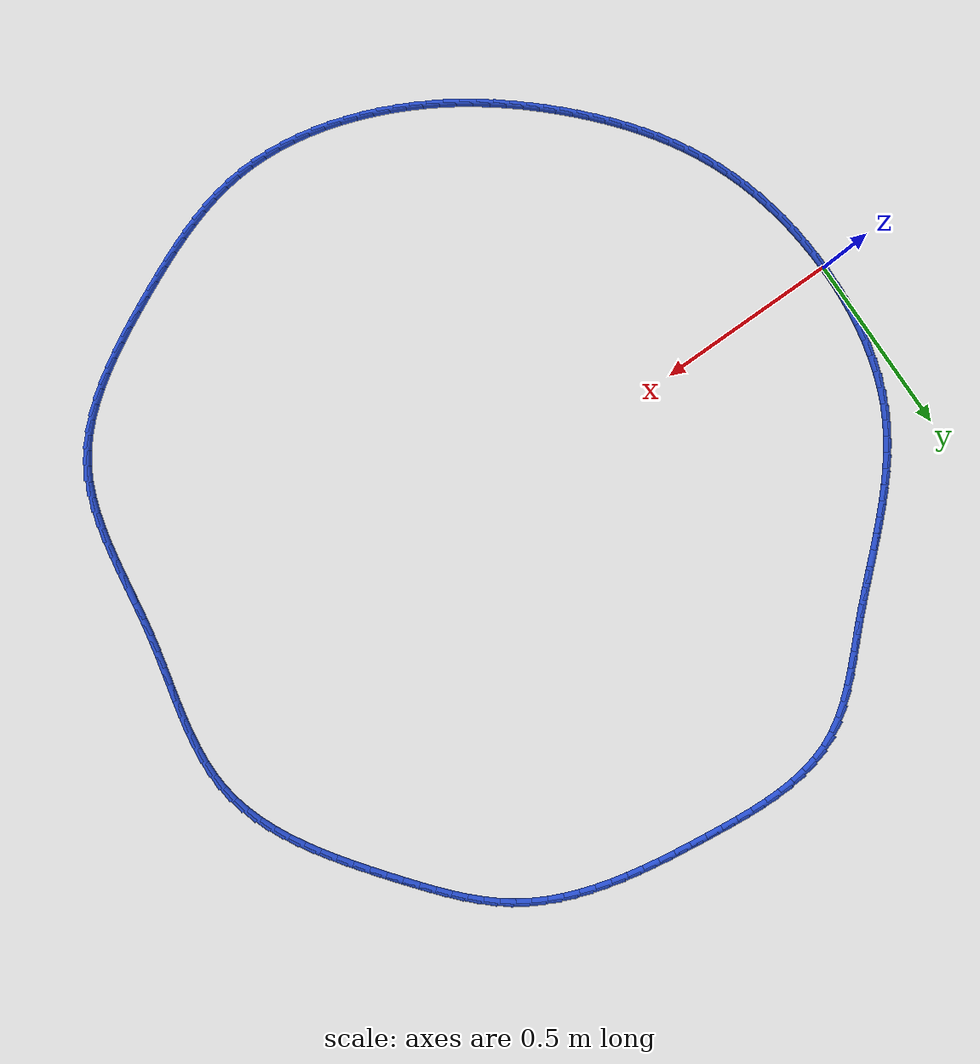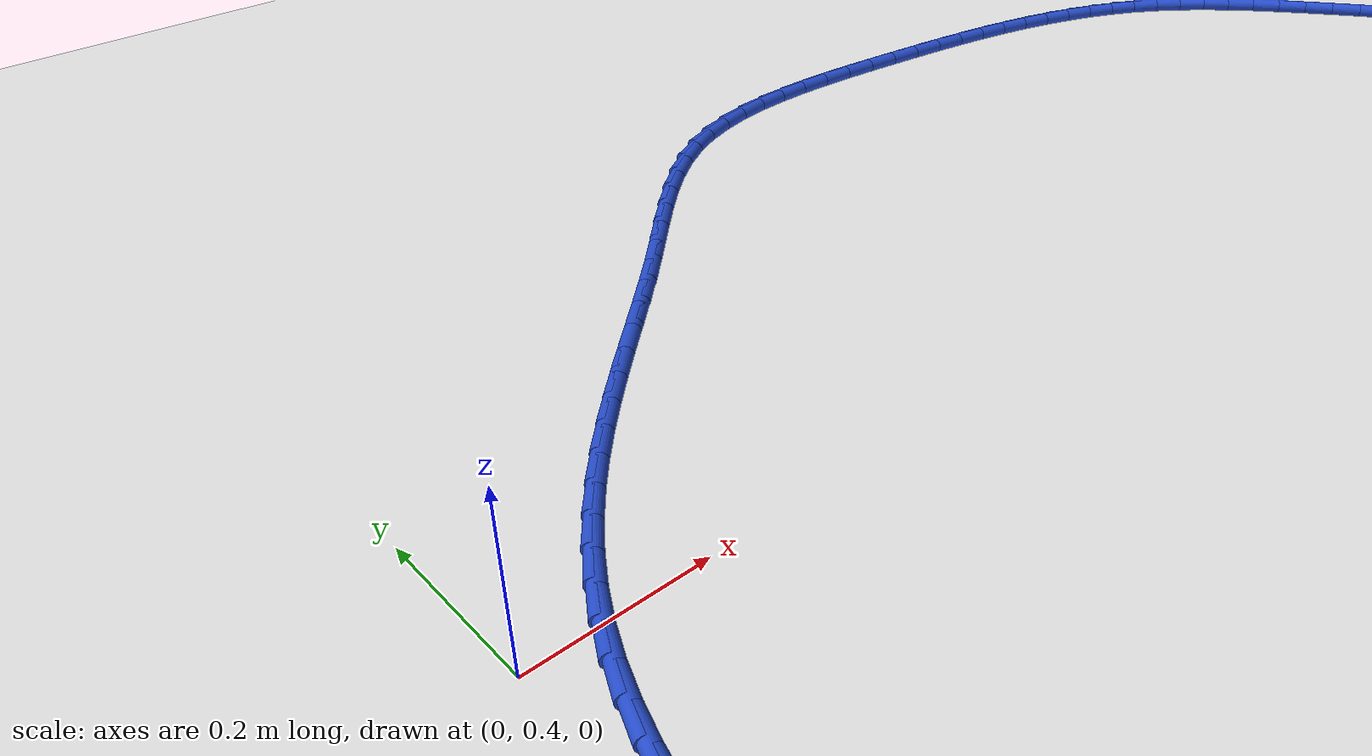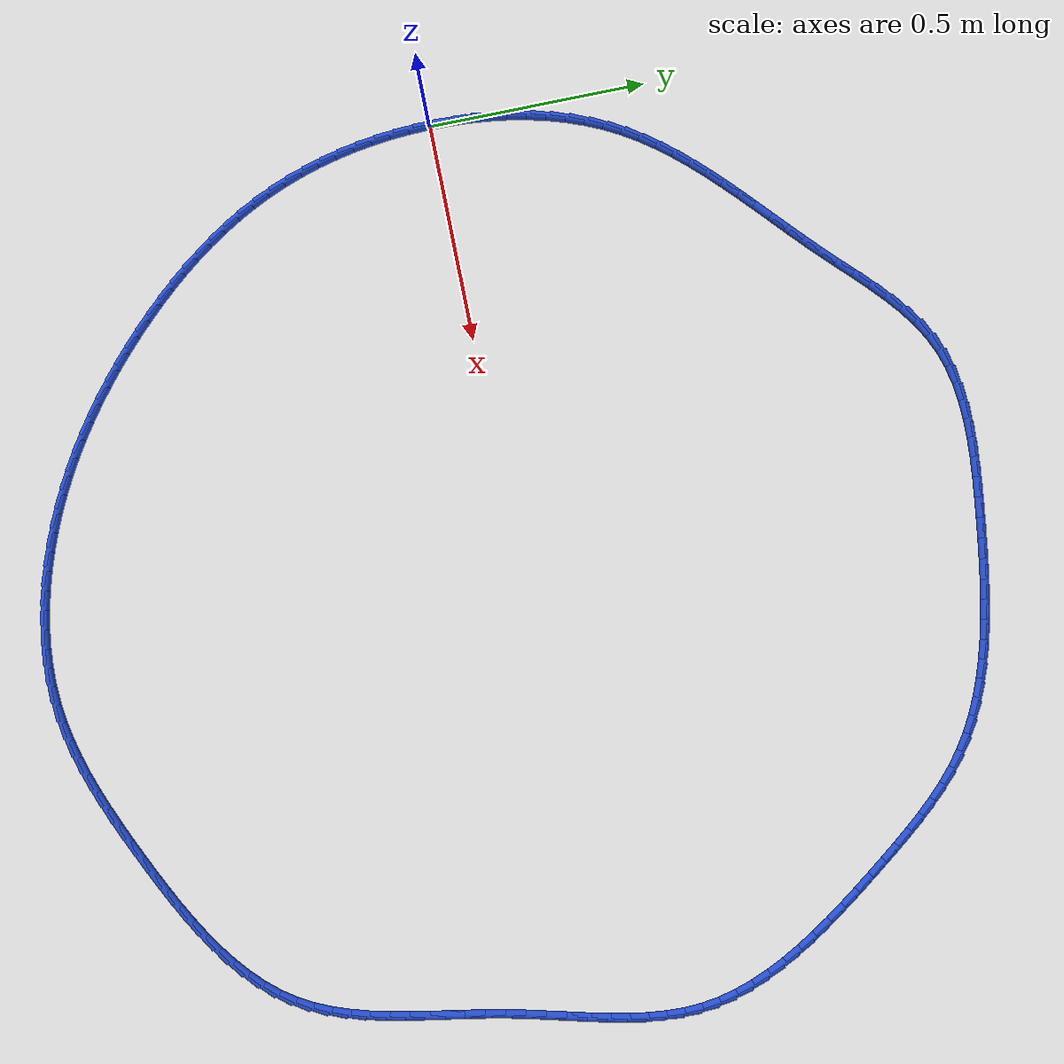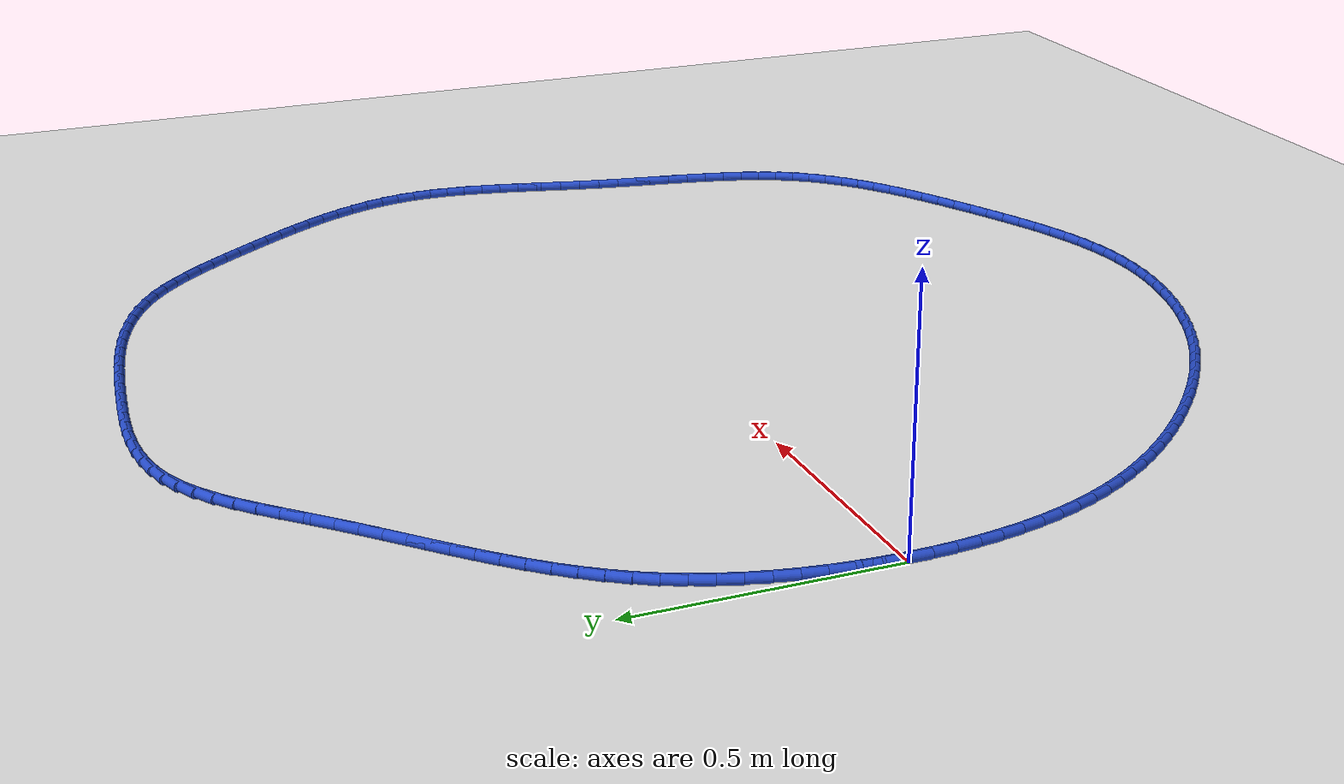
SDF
<sdf version="1.6">
 <world name="default">
  <light name="sun" type="directional">
   <pose>0 0 10 0 -0 0</pose>
   <diffuse>0.8 0.8 0.8 1</diffuse>
   <specular>0.2 0.2 0.2 1</specular>
   <attenuation>
    <range>1000</range>
    <constant>0.9</constant>
    <linear>0.01</linear>
    <quadratic>0.001</quadratic>
   </attenuation>
   <direction>-0.5 0.1 -0.9</direction>
  </light>
  <model name="ground_plane">
   <static>1</static>
   <link name="link">
    <collision name="collision">
     <geometry><plane><normal>0 0 1</normal><size>100 100</size></plane></geometry>
     <surface><friction><ode><mu>100</mu><mu2>50</mu2></ode></friction></surface>
    </collision>
    <visual name="visual">
     <cast_shadows>0</cast_shadows>
     <geometry><plane><normal>0 0 1</normal><size>100 100</size></plane></geometry>
     <material>
      <script><uri>file://media/materials/scripts/gazebo.material</uri><name>Gazebo/WhiteGlow</name></script>
     </material>
    </visual>
   </link>
  </model>
  <gravity>0 0 -9.8</gravity>
  <magnetic_field>6e-06 2.3e-05 -4.2e-05</magnetic_field>
  <atmosphere type="adiabatic"/>
  <physics name="default_physics" default="0" type="ode">
   <max_step_size>0.001</max_step_size>
   <real_time_factor>1</real_time_factor>
   <real_time_update_rate>1000</real_time_update_rate>
  </physics>
  <scene><ambient>0.4 0.4 0.4 1</ambient><background>0.7 0.7 0.7 1</background><shadows>1</shadows></scene>
  <spherical_coordinates>
   <surface_model>EARTH_WGS84</surface_model>
   <latitude_deg>0</latitude_deg>
   <longitude_deg>0</longitude_deg>
   <elevation>0</elevation>
   <heading_deg>0</heading_deg>
  </spherical_coordinates>
  <model name="line">
   <link name="link_0">
    <pose>-3.469446951953614e-18 -8.326672684688674e-17 0.01 0 1.57 1.5598164352984312</pose>
    <collision name="collision">
     <geometry><cylinder><radius>0.01</radius><length>0.08</length></cylinder></geometry>
    </collision>
    <visual name="visual">
     <material>
      <script><name>Gazebo/Blue</name><uri>file://media/materials/scripts/gazebo.material</uri></script>
     </material>
     <geometry><cylinder><radius>0.01</radius><length>0.08</length></cylinder></geometry>
    </visual>
   </link>
   <link name="link_1">
    <pose>0.0004980837336147178 0.04536144256237778 0.01 0 1.57 1.5186307544797466</pose>
    <collision name="collision">
     <geometry><cylinder><radius>0.01</radius><length>0.08</length></cylinder></geometry>
    </collision>
    <visual name="visual">
     <material>
      <script><name>Gazebo/Blue</name><uri>file://media/materials/scripts/gazebo.material</uri></script>
     </material>
     <geometry><cylinder><radius>0.01</radius><length>0.08</length></cylinder></geometry>
    </visual>
   </link>
   <link name="link_2">
    <pose>0.0028660589533701453 0.09071370798471727 0.01 0 1.57 1.4754094035959286</pose>
    <collision name="collision">
     <geometry><cylinder><radius>0.01</radius><length>0.08</length></cylinder></geometry>
    </collision>
    <visual name="visual">
     <material>
      <script><name>Gazebo/Blue</name><uri>file://media/materials/scripts/gazebo.material</uri></script>
     </material>
     <geometry><cylinder><radius>0.01</radius><length>0.08</length></cylinder></geometry>
    </visual>
   </link>
   <link name="link_3">
    <pose>0.007185367812581252 0.13585827057391336 0.01 0 1.57 1.4297559981222152</pose>
    <collision name="collision">
     <geometry><cylinder><radius>0.01</radius><length>0.08</length></cylinder></geometry>
    </collision>
    <visual name="visual">
     <material>
      <script><name>Gazebo/Blue</name><uri>file://media/materials/scripts/gazebo.material</uri></script>
     </material>
     <geometry><cylinder><radius>0.01</radius><length>0.08</length></cylinder></geometry>
    </visual>
   </link>
   <link name="link_4">
    <pose>0.013537452464563046 0.18059660463686114 0.01 0 1.57 1.381265283397986</pose>
    <collision name="collision">
     <geometry><cylinder><radius>0.01</radius><length>0.08</length></cylinder></geometry>
    </collision>
    <visual name="visual">
     <material>
      <script><name>Gazebo/Blue</name><uri>file://media/materials/scripts/gazebo.material</uri></script>
     </material>
     <geometry><cylinder><radius>0.01</radius><length>0.08</length></cylinder></geometry>
    </visual>
   </link>
   <link name="link_5">
    <pose>0.02200375506263049 0.22473018448045545 0.01 0 1.57 1.32952694881339</pose>
    <collision name="collision">
     <geometry><cylinder><radius>0.01</radius><length>0.08</length></cylinder></geometry>
    </collision>
    <visual name="visual">
     <material>
      <script><name>Gazebo/Blue</name><uri>file://media/materials/scripts/gazebo.material</uri></script>
     </material>
     <geometry><cylinder><radius>0.01</radius><length>0.08</length></cylinder></geometry>
    </visual>
   </link>
   <link name="link_6">
    <pose>0.03266571776009861 0.2680604844115916 0.01 0 1.57 1.2741347418427678</pose>
    <collision name="collision">
     <geometry><cylinder><radius>0.01</radius><length>0.08</length></cylinder></geometry>
    </collision>
    <visual name="visual">
     <material>
      <script><name>Gazebo/Blue</name><uri>file://media/materials/scripts/gazebo.material</uri></script>
     </material>
     <geometry><cylinder><radius>0.01</radius><length>0.08</length></cylinder></geometry>
    </visual>
   </link>
   <link name="link_7">
    <pose>0.045604782710282385 0.31038897873716437 0.01 0 1.57 1.2147025391484945</pose>
    <collision name="collision">
     <geometry><cylinder><radius>0.01</radius><length>0.08</length></cylinder></geometry>
    </collision>
    <visual name="visual">
     <material>
      <script><name>Gazebo/Blue</name><uri>file://media/materials/scripts/gazebo.material</uri></script>
     </material>
     <geometry><cylinder><radius>0.01</radius><length>0.08</length></cylinder></geometry>
    </visual>
   </link>
   <link name="link_8">
    <pose>0.060902392066496794 0.35151714176406873 0.01 0 1.57 1.1508891159409884</pose>
    <collision name="collision">
     <geometry><cylinder><radius>0.01</radius><length>0.08</length></cylinder></geometry>
    </collision>
    <visual name="visual">
     <material>
      <script><name>Gazebo/Blue</name><uri>file://media/materials/scripts/gazebo.material</uri></script>
     </material>
     <geometry><cylinder><radius>0.01</radius><length>0.08</length></cylinder></geometry>
    </visual>
   </link>
   <link name="link_9">
    <pose>0.07863998798205683 0.3912464477991998 0.01 0 1.57 1.08282353586346</pose>
    <collision name="collision">
     <geometry><cylinder><radius>0.01</radius><length>0.08</length></cylinder></geometry>
    </collision>
    <visual name="visual">
     <material>
      <script><name>Gazebo/Blue</name><uri>file://media/materials/scripts/gazebo.material</uri></script>
     </material>
     <geometry><cylinder><radius>0.01</radius><length>0.08</length></cylinder></geometry>
    </visual>
   </link>
   <link name="link_10">
    <pose>0.09888734159345738 0.4293923587249024 0.01 0 1.57 1.0164514166122463</pose>
    <collision name="collision">
     <geometry><cylinder><radius>0.01</radius><length>0.08</length></cylinder></geometry>
    </collision>
    <visual name="visual">
     <material>
      <script><name>Gazebo/Blue</name><uri>file://media/materials/scripts/gazebo.material</uri></script>
     </material>
     <geometry><cylinder><radius>0.01</radius><length>0.08</length></cylinder></geometry>
    </visual>
   </link>
   <link name="link_11">
    <pose>0.12153896443427915 0.4659803829821774 0.01 0 1.57 0.9569753983589105</pose>
    <collision name="collision">
     <geometry><cylinder><radius>0.01</radius><length>0.08</length></cylinder></geometry>
    </collision>
    <visual name="visual">
     <material>
      <script><name>Gazebo/Blue</name><uri>file://media/materials/scripts/gazebo.material</uri></script>
     </material>
     <geometry><cylinder><radius>0.01</radius><length>0.08</length></cylinder></geometry>
    </visual>
   </link>
   <link name="link_12">
    <pose>0.1463541316501552 0.5011981082215012 0.01 0 1.57 0.9050196701007648</pose>
    <collision name="collision">
     <geometry><cylinder><radius>0.01</radius><length>0.08</length></cylinder></geometry>
    </collision>
    <visual name="visual">
     <material>
      <script><name>Gazebo/Blue</name><uri>file://media/materials/scripts/gazebo.material</uri></script>
     </material>
     <geometry><cylinder><radius>0.01</radius><length>0.08</length></cylinder></geometry>
    </visual>
   </link>
   <link name="link_13">
    <pose>0.17308862103365819 0.535237313629578 0.01 0 1.57 0.8607954842290533</pose>
    <collision name="collision">
     <geometry><cylinder><radius>0.01</radius><length>0.08</length></cylinder></geometry>
    </collision>
    <visual name="visual">
     <material>
      <script><name>Gazebo/Blue</name><uri>file://media/materials/scripts/gazebo.material</uri></script>
     </material>
     <geometry><cylinder><radius>0.01</radius><length>0.08</length></cylinder></geometry>
    </visual>
   </link>
   <link name="link_14">
    <pose>0.2014982103773606 0.5682897783931119 0.01 0 1.57 0.8243014754025475</pose>
    <collision name="collision">
     <geometry><cylinder><radius>0.01</radius><length>0.08</length></cylinder></geometry>
    </collision>
    <visual name="visual">
     <material>
      <script><name>Gazebo/Blue</name><uri>file://media/materials/scripts/gazebo.material</uri></script>
     </material>
     <geometry><cylinder><radius>0.01</radius><length>0.08</length></cylinder></geometry>
    </visual>
   </link>
   <link name="link_15">
    <pose>0.23133867747383494 0.6005472816988067 0.01 0 1.57 0.795403954983912</pose>
    <collision name="collision">
     <geometry><cylinder><radius>0.01</radius><length>0.08</length></cylinder></geometry>
    </collision>
    <visual name="visual">
     <material>
      <script><name>Gazebo/Blue</name><uri>file://media/materials/scripts/gazebo.material</uri></script>
     </material>
     <geometry><cylinder><radius>0.01</radius><length>0.08</length></cylinder></geometry>
    </visual>
   </link>
   <link name="link_16">
    <pose>0.2623658001156538 0.6322016027333663 0.01 0 1.57 0.773903501327503</pose>
    <collision name="collision">
     <geometry><cylinder><radius>0.01</radius><length>0.08</length></cylinder></geometry>
    </collision>
    <visual name="visual">
     <material>
      <script><name>Gazebo/Blue</name><uri>file://media/materials/scripts/gazebo.material</uri></script>
     </material>
     <geometry><cylinder><radius>0.01</radius><length>0.08</length></cylinder></geometry>
    </visual>
   </link>
   <link name="link_17">
    <pose>0.29433535609538963 0.6634445206834949 0.01 0 1.57 0.7595843718589559</pose>
    <collision name="collision">
     <geometry><cylinder><radius>0.01</radius><length>0.08</length></cylinder></geometry>
    </collision>
    <visual name="visual">
     <material>
      <script><name>Gazebo/Blue</name><uri>file://media/materials/scripts/gazebo.material</uri></script>
     </material>
     <geometry><cylinder><radius>0.01</radius><length>0.08</length></cylinder></geometry>
    </visual>
   </link>
   <link name="link_18">
    <pose>0.32700312320561503 0.6944678147358964 0.01 0 1.57 0.7522475026773017</pose>
    <collision name="collision">
     <geometry><cylinder><radius>0.01</radius><length>0.08</length></cylinder></geometry>
    </collision>
    <visual name="visual">
     <material>
      <script><name>Gazebo/Blue</name><uri>file://media/materials/scripts/gazebo.material</uri></script>
     </material>
     <geometry><cylinder><radius>0.01</radius><length>0.08</length></cylinder></geometry>
    </visual>
   </link>
   <link name="link_19">
    <pose>0.36012487923890246 0.7254632640772747 0.01 0 1.57 0.7517295700213301</pose>
    <collision name="collision">
     <geometry><cylinder><radius>0.01</radius><length>0.08</length></cylinder></geometry>
    </collision>
    <visual name="visual">
     <material>
      <script><name>Gazebo/Blue</name><uri>file://media/materials/scripts/gazebo.material</uri></script>
     </material>
     <geometry><cylinder><radius>0.01</radius><length>0.08</length></cylinder></geometry>
    </visual>
   </link>
   <link name="link_20">
    <pose>0.39345640198782456 0.7566226478943339 0.01 0 1.57 0.7579107161345098</pose>
    <collision name="collision">
     <geometry><cylinder><radius>0.01</radius><length>0.08</length></cylinder></geometry>
    </collision>
    <visual name="visual">
     <material>
      <script><name>Gazebo/Blue</name><uri>file://media/materials/scripts/gazebo.material</uri></script>
     </material>
     <geometry><cylinder><radius>0.01</radius><length>0.08</length></cylinder></geometry>
    </visual>
   </link>
   <link name="link_21">
    <pose>0.4267534692449537 0.7881377453737778 0.01 0 1.57 0.7707129124697559</pose>
    <collision name="collision">
     <geometry><cylinder><radius>0.01</radius><length>0.08</length></cylinder></geometry>
    </collision>
    <visual name="visual">
     <material>
      <script><name>Gazebo/Blue</name><uri>file://media/materials/scripts/gazebo.material</uri></script>
     </material>
     <geometry><cylinder><radius>0.01</radius><length>0.08</length></cylinder></geometry>
    </visual>
   </link>
   <link name="link_22">
    <pose>0.45977185880286264 0.8202003357023107 0.01 0 1.57 0.7874714968516009</pose>
    <collision name="collision">
     <geometry><cylinder><radius>0.01</radius><length>0.08</length></cylinder></geometry>
    </collision>
    <visual name="visual">
     <material>
      <script><name>Gazebo/Blue</name><uri>file://media/materials/scripts/gazebo.material</uri></script>
     </material>
     <geometry><cylinder><radius>0.01</radius><length>0.08</length></cylinder></geometry>
    </visual>
   </link>
   <link name="link_23">
    <pose>0.4923334600405235 0.8528972397760777 0.01 0 1.57 0.7929929778401426</pose>
    <collision name="collision">
     <geometry><cylinder><radius>0.01</radius><length>0.08</length></cylinder></geometry>
    </collision>
    <visual name="visual">
     <material>
      <script><name>Gazebo/Blue</name><uri>file://media/materials/scripts/gazebo.material</uri></script>
     </material>
     <geometry><cylinder><radius>0.01</radius><length>0.08</length></cylinder></geometry>
    </visual>
   </link>
   <link name="link_24">
    <pose>0.5246453715996344 0.8857037229693384 0.01 0 1.57 0.7817123978896611</pose>
    <collision name="collision">
     <geometry><cylinder><radius>0.01</radius><length>0.08</length></cylinder></geometry>
    </collision>
    <visual name="visual">
     <material>
      <script><name>Gazebo/Blue</name><uri>file://media/materials/scripts/gazebo.material</uri></script>
     </material>
     <geometry><cylinder><radius>0.01</radius><length>0.08</length></cylinder></geometry>
    </visual>
   </link>
   <link name="link_25">
    <pose>0.5570538294970856 0.9178741571360471 0.01 0 1.57 0.7529931709062846</pose>
    <collision name="collision">
     <geometry><cylinder><radius>0.01</radius><length>0.08</length></cylinder></geometry>
    </collision>
    <visual name="visual">
     <material>
      <script><name>Gazebo/Blue</name><uri>file://media/materials/scripts/gazebo.material</uri></script>
     </material>
     <geometry><cylinder><radius>0.01</radius><length>0.08</length></cylinder></geometry>
    </visual>
   </link>
   <link name="link_26">
    <pose>0.589905258699434 0.9486626141549902 0.01 0 1.57 0.7056293653462783</pose>
    <collision name="collision">
     <geometry><cylinder><radius>0.01</radius><length>0.08</length></cylinder></geometry>
    </collision>
    <visual name="visual">
     <material>
      <script><name>Gazebo/Blue</name><uri>file://media/materials/scripts/gazebo.material</uri></script>
     </material>
     <geometry><cylinder><radius>0.01</radius><length>0.08</length></cylinder></geometry>
    </visual>
   </link>
   <link name="link_27">
    <pose>0.6235460841732369 0.9773231659049542 0.01 0 1.57 0.6380358123388974</pose>
    <collision name="collision">
     <geometry><cylinder><radius>0.01</radius><length>0.08</length></cylinder></geometry>
    </collision>
    <visual name="visual">
     <material>
      <script><name>Gazebo/Blue</name><uri>file://media/materials/scripts/gazebo.material</uri></script>
     </material>
     <geometry><cylinder><radius>0.01</radius><length>0.08</length></cylinder></geometry>
    </visual>
   </link>
   <link name="link_28">
    <pose>0.6583227308850517 1.003109884264726 0.01 0 1.57 0.5487249761104109</pose>
    <collision name="collision">
     <geometry><cylinder><radius>0.01</radius><length>0.08</length></cylinder></geometry>
    </collision>
    <visual name="visual">
     <material>
      <script><name>Gazebo/Blue</name><uri>file://media/materials/scripts/gazebo.material</uri></script>
     </material>
     <geometry><cylinder><radius>0.01</radius><length>0.08</length></cylinder></geometry>
    </visual>
   </link>
   <link name="link_29">
    <pose>0.6945816238014362 1.0252768411130926 0.01 0 1.57 0.4376581873895233</pose>
    <collision name="collision">
     <geometry><cylinder><radius>0.01</radius><length>0.08</length></cylinder></geometry>
    </collision>
    <visual name="visual">
     <material>
      <script><name>Gazebo/Blue</name><uri>file://media/materials/scripts/gazebo.material</uri></script>
     </material>
     <geometry><cylinder><radius>0.01</radius><length>0.08</length></cylinder></geometry>
    </visual>
   </link>
   <link name="link_30">
    <pose>0.7326611927867951 1.043095140949543 0.01 0 1.57 0.32077157145601176</pose>
    <collision name="collision">
     <geometry><cylinder><radius>0.01</radius><length>0.08</length></cylinder></geometry>
    </collision>
    <visual name="visual">
     <material>
      <script><name>Gazebo/Blue</name><uri>file://media/materials/scripts/gazebo.material</uri></script>
     </material>
     <geometry><cylinder><radius>0.01</radius><length>0.08</length></cylinder></geometry>
    </visual>
   </link>
   <link name="link_31">
    <pose>0.7726446977582366 1.05637949770398 0.01 0 1.57 0.21752228846156565</pose>
    <collision name="collision">
     <geometry><cylinder><radius>0.01</radius><length>0.08</length></cylinder></geometry>
    </collision>
    <visual name="visual">
     <material>
      <script><name>Gazebo/Blue</name><uri>file://media/materials/scripts/gazebo.material</uri></script>
     </material>
     <geometry><cylinder><radius>0.01</radius><length>0.08</length></cylinder></geometry>
    </visual>
   </link>
   <link name="link_32">
    <pose>0.8143129385195773 1.0655889808491543 0.01 0 1.57 0.12986642397919734</pose>
    <collision name="collision">
     <geometry><cylinder><radius>0.01</radius><length>0.08</length></cylinder></geometry>
    </collision>
    <visual name="visual">
     <material>
      <script><name>Gazebo/Blue</name><uri>file://media/materials/scripts/gazebo.material</uri></script>
     </material>
     <geometry><cylinder><radius>0.01</radius><length>0.08</length></cylinder></geometry>
    </visual>
   </link>
   <link name="link_33">
    <pose>0.8574291759518371 1.0712200244610264 0.01 0 1.57 0.05744141435829287</pose>
    <collision name="collision">
     <geometry><cylinder><radius>0.01</radius><length>0.08</length></cylinder></geometry>
    </collision>
    <visual name="visual">
     <material>
      <script><name>Gazebo/Blue</name><uri>file://media/materials/scripts/gazebo.material</uri></script>
     </material>
     <geometry><cylinder><radius>0.01</radius><length>0.08</length></cylinder></geometry>
    </visual>
   </link>
   <link name="link_34">
    <pose>0.9017566709360358 1.0737690626155552 0.01 0 1.57 -0.00080643698102957</pose>
    <collision name="collision">
     <geometry><cylinder><radius>0.01</radius><length>0.08</length></cylinder></geometry>
    </collision>
    <visual name="visual">
     <material>
      <script><name>Gazebo/Blue</name><uri>file://media/materials/scripts/gazebo.material</uri></script>
     </material>
     <geometry><cylinder><radius>0.01</radius><length>0.08</length></cylinder></geometry>
    </visual>
   </link>
   <link name="link_35">
    <pose>0.947058684353193 1.0737325293887008 0.01 0 1.57 -0.04613752381808575</pose>
    <collision name="collision">
     <geometry><cylinder><radius>0.01</radius><length>0.08</length></cylinder></geometry>
    </collision>
    <visual name="visual">
     <material>
      <script><name>Gazebo/Blue</name><uri>file://media/materials/scripts/gazebo.material</uri></script>
     </material>
     <geometry><cylinder><radius>0.01</radius><length>0.08</length></cylinder></geometry>
    </visual>
   </link>
   <link name="link_36">
    <pose>0.993098477084329 1.0716068588564225 0.01 0 1.57 -0.07972552265454705</pose>
    <collision name="collision">
     <geometry><cylinder><radius>0.01</radius><length>0.08</length></cylinder></geometry>
    </collision>
    <visual name="visual">
     <material>
      <script><name>Gazebo/Blue</name><uri>file://media/materials/scripts/gazebo.material</uri></script>
     </material>
     <geometry><cylinder><radius>0.01</radius><length>0.08</length></cylinder></geometry>
    </visual>
   </link>
   <link name="link_37">
    <pose>1.0396393100104626 1.06788848509468 0.01 0 1.57 -0.10250516770148083</pose>
    <collision name="collision">
     <geometry><cylinder><radius>0.01</radius><length>0.08</length></cylinder></geometry>
    </collision>
    <visual name="visual">
     <material>
      <script><name>Gazebo/Blue</name><uri>file://media/materials/scripts/gazebo.material</uri></script>
     </material>
     <geometry><cylinder><radius>0.01</radius><length>0.08</length></cylinder></geometry>
    </visual>
   </link>
   <link name="link_38">
    <pose>1.0864444440126149 1.063073842179433 0.01 0 1.57 -0.11516826157743802</pose>
    <collision name="collision">
     <geometry><cylinder><radius>0.01</radius><length>0.08</length></cylinder></geometry>
    </collision>
    <visual name="visual">
     <material>
      <script><name>Gazebo/Blue</name><uri>file://media/materials/scripts/gazebo.material</uri></script>
     </material>
     <geometry><cylinder><radius>0.01</radius><length>0.08</length></cylinder></geometry>
    </visual>
   </link>
   <link name="link_39">
    <pose>1.1332775977782665 1.0576561752479672 0.01 0 1.57 -0.12310397523829378</pose>
    <collision name="collision">
     <geometry><cylinder><radius>0.01</radius><length>0.08</length></cylinder></geometry>
    </collision>
    <visual name="visual">
     <material>
      <script><name>Gazebo/Blue</name><uri>file://media/materials/scripts/gazebo.material</uri></script>
     </material>
     <geometry><cylinder><radius>0.01</radius><length>0.08</length></cylinder></geometry>
    </visual>
   </link>
   <link name="link_40">
    <pose>1.1799377773759128 1.0518829284202045 0.01 0 1.57 -0.1350533147623352</pose>
    <collision name="collision">
     <geometry><cylinder><radius>0.01</radius><length>0.08</length></cylinder></geometry>
    </collision>
    <visual name="visual">
     <material>
      <script><name>Gazebo/Blue</name><uri>file://media/materials/scripts/gazebo.material</uri></script>
     </material>
     <geometry><cylinder><radius>0.01</radius><length>0.08</length></cylinder></geometry>
    </visual>
   </link>
   <link name="link_41">
    <pose>1.2262837282260395 1.0455854199071946 0.01 0 1.57 -0.15200506149876847</pose>
    <collision name="collision">
     <geometry><cylinder><radius>0.01</radius><length>0.08</length></cylinder></geometry>
    </collision>
    <visual name="visual">
     <material>
      <script><name>Gazebo/Blue</name><uri>file://media/materials/scripts/gazebo.material</uri></script>
     </material>
     <geometry><cylinder><radius>0.01</radius><length>0.08</length></cylinder></geometry>
    </visual>
   </link>
   <link name="link_42">
    <pose>1.2721799729846093 1.0385547254787244 0.01 0 1.57 -0.17417420988629273</pose>
    <collision name="collision">
     <geometry><cylinder><radius>0.01</radius><length>0.08</length></cylinder></geometry>
    </collision>
    <visual name="visual">
     <material>
      <script><name>Gazebo/Blue</name><uri>file://media/materials/scripts/gazebo.material</uri></script>
     </material>
     <geometry><cylinder><radius>0.01</radius><length>0.08</length></cylinder></geometry>
    </visual>
   </link>
   <link name="link_43">
    <pose>1.3174910343075843 1.03058192090458 0.01 0 1.57 -0.201828539432627</pose>
    <collision name="collision">
     <geometry><cylinder><radius>0.01</radius><length>0.08</length></cylinder></geometry>
    </collision>
    <visual name="visual">
     <material>
      <script><name>Gazebo/Blue</name><uri>file://media/materials/scripts/gazebo.material</uri></script>
     </material>
     <geometry><cylinder><radius>0.01</radius><length>0.08</length></cylinder></geometry>
    </visual>
   </link>
   <link name="link_44">
    <pose>1.362081434850928 1.0214580819545478 0.01 0 1.57 -0.23527632506989113</pose>
    <collision name="collision">
     <geometry><cylinder><radius>0.01</radius><length>0.08</length></cylinder></geometry>
    </collision>
    <visual name="visual">
     <material>
      <script><name>Gazebo/Blue</name><uri>file://media/materials/scripts/gazebo.material</uri></script>
     </material>
     <geometry><cylinder><radius>0.01</radius><length>0.08</length></cylinder></geometry>
    </visual>
   </link>
   <link name="link_45">
    <pose>1.4058156972706037 1.0109742843984144 0.01 0 1.57 -0.27484616910155496</pose>
    <collision name="collision">
     <geometry><cylinder><radius>0.01</radius><length>0.08</length></cylinder></geometry>
    </collision>
    <visual name="visual">
     <material>
      <script><name>Gazebo/Blue</name><uri>file://media/materials/scripts/gazebo.material</uri></script>
     </material>
     <geometry><cylinder><radius>0.01</radius><length>0.08</length></cylinder></geometry>
    </visual>
   </link>
   <link name="link_46">
    <pose>1.4485583442225725 0.9989216040059661 0.01 0 1.57 -0.32085572976055443</pose>
    <collision name="collision">
     <geometry><cylinder><radius>0.01</radius><length>0.08</length></cylinder></geometry>
    </collision>
    <visual name="visual">
     <material>
      <script><name>Gazebo/Blue</name><uri>file://media/materials/scripts/gazebo.material</uri></script>
     </material>
     <geometry><cylinder><radius>0.01</radius><length>0.08</length></cylinder></geometry>
    </visual>
   </link>
   <link name="link_47">
    <pose>1.4901738983627983 0.9850911165469892 0.01 0 1.57 -0.3735661344318423</pose>
    <collision name="collision">
     <geometry><cylinder><radius>0.01</radius><length>0.08</length></cylinder></geometry>
    </collision>
    <visual name="visual">
     <material>
      <script><name>Gazebo/Blue</name><uri>file://media/materials/scripts/gazebo.material</uri></script>
     </material>
     <geometry><cylinder><radius>0.01</radius><length>0.08</length></cylinder></geometry>
    </visual>
   </link>
   <link name="link_48">
    <pose>1.530526882347243 0.9692738977912702 0.01 0 1.57 -0.43312014791408227</pose>
    <collision name="collision">
     <geometry><cylinder><radius>0.01</radius><length>0.08</length></cylinder></geometry>
    </collision>
    <visual name="visual">
     <material>
      <script><name>Gazebo/Blue</name><uri>file://media/materials/scripts/gazebo.material</uri></script>
     </material>
     <geometry><cylinder><radius>0.01</radius><length>0.08</length></cylinder></geometry>
    </visual>
   </link>
   <link name="link_49">
    <pose>1.5694818188318709 0.9512610235085959 0.01 0 1.57 -0.49946565035677365</pose>
    <collision name="collision">
     <geometry><cylinder><radius>0.01</radius><length>0.08</length></cylinder></geometry>
    </collision>
    <visual name="visual">
     <material>
      <script><name>Gazebo/Blue</name><uri>file://media/materials/scripts/gazebo.material</uri></script>
     </material>
     <geometry><cylinder><radius>0.01</radius><length>0.08</length></cylinder></geometry>
    </visual>
   </link>
   <link name="link_50">
    <pose>1.6069032304726434 0.9308435694687521 0.01 0 1.57 -0.5722723704274157</pose>
    <collision name="collision">
     <geometry><cylinder><radius>0.01</radius><length>0.08</length></cylinder></geometry>
    </collision>
    <visual name="visual">
     <material>
      <script><name>Gazebo/Blue</name><uri>file://media/materials/scripts/gazebo.material</uri></script>
     </material>
     <geometry><cylinder><radius>0.01</radius><length>0.08</length></cylinder></geometry>
    </visual>
   </link>
   <link name="link_51">
    <pose>1.6426556399255228 0.9078126114415256 0.01 0 1.57 -0.6495528864928601</pose>
    <collision name="collision">
     <geometry><cylinder><radius>0.01</radius><length>0.08</length></cylinder></geometry>
    </collision>
    <visual name="visual">
     <material>
      <script><name>Gazebo/Blue</name><uri>file://media/materials/scripts/gazebo.material</uri></script>
     </material>
     <geometry><cylinder><radius>0.01</radius><length>0.08</length></cylinder></geometry>
    </visual>
   </link>
   <link name="link_52">
    <pose>1.6766363597591805 0.8820042841685876 0.01 0 1.57 -0.720430150250718</pose>
    <collision name="collision">
     <geometry><cylinder><radius>0.01</radius><length>0.08</length></cylinder></geometry>
    </collision>
    <visual name="visual">
     <material>
      <script><name>Gazebo/Blue</name><uri>file://media/materials/scripts/gazebo.material</uri></script>
     </material>
     <geometry><cylinder><radius>0.01</radius><length>0.08</length></cylinder></geometry>
    </visual>
   </link>
   <link name="link_53">
    <pose>1.7089938905427677 0.8535998978470134 0.01 0 1.57 -0.7798929273951475</pose>
    <collision name="collision">
     <geometry><cylinder><radius>0.01</radius><length>0.08</length></cylinder></geometry>
    </collision>
    <visual name="visual">
     <material>
      <script><name>Gazebo/Blue</name><uri>file://media/materials/scripts/gazebo.material</uri></script>
     </material>
     <geometry><cylinder><radius>0.01</radius><length>0.08</length></cylinder></geometry>
    </visual>
   </link>
   <link name="link_54">
    <pose>1.7399928748245117 0.8229403617010722 0.01 0 1.57 -0.8280621258734835</pose>
    <collision name="collision">
     <geometry><cylinder><radius>0.01</radius><length>0.08</length></cylinder></geometry>
    </collision>
    <visual name="visual">
     <material>
      <script><name>Gazebo/Blue</name><uri>file://media/materials/scripts/gazebo.material</uri></script>
     </material>
     <geometry><cylinder><radius>0.01</radius><length>0.08</length></cylinder></geometry>
    </visual>
   </link>
   <link name="link_55">
    <pose>1.7698985837290366 0.7903674487269619 0.01 0 1.57 -0.8653701384699545</pose>
    <collision name="collision">
     <geometry><cylinder><radius>0.01</radius><length>0.08</length></cylinder></geometry>
    </collision>
    <visual name="visual">
     <material>
      <script><name>Gazebo/Blue</name><uri>file://media/materials/scripts/gazebo.material</uri></script>
     </material>
     <geometry><cylinder><radius>0.01</radius><length>0.08</length></cylinder></geometry>
    </visual>
   </link>
   <link name="link_56">
    <pose>1.7989762883809655 0.7562229319208784 0.01 0 1.57 -0.8923518953793831</pose>
    <collision name="collision">
     <geometry><cylinder><radius>0.01</radius><length>0.08</length></cylinder></geometry>
    </collision>
    <visual name="visual">
     <material>
      <script><name>Gazebo/Blue</name><uri>file://media/materials/scripts/gazebo.material</uri></script>
     </material>
     <geometry><cylinder><radius>0.01</radius><length>0.08</length></cylinder></geometry>
    </visual>
   </link>
   <link name="link_57">
    <pose>1.827491259904921 0.7208485842790184 0.01 0 1.57 -0.9095226732119822</pose>
    <collision name="collision">
     <geometry><cylinder><radius>0.01</radius><length>0.08</length></cylinder></geometry>
    </collision>
    <visual name="visual">
     <material>
      <script><name>Gazebo/Blue</name><uri>file://media/materials/scripts/gazebo.material</uri></script>
     </material>
     <geometry><cylinder><radius>0.01</radius><length>0.08</length></cylinder></geometry>
    </visual>
   </link>
   <link name="link_58">
    <pose>1.8557087694255268 0.6845861787975789 0.01 0 1.57 -0.9181744254247517</pose>
    <collision name="collision">
     <geometry><cylinder><radius>0.01</radius><length>0.08</length></cylinder></geometry>
    </collision>
    <visual name="visual">
     <material>
      <script><name>Gazebo/Blue</name><uri>file://media/materials/scripts/gazebo.material</uri></script>
     </material>
     <geometry><cylinder><radius>0.01</radius><length>0.08</length></cylinder></geometry>
    </visual>
   </link>
   <link name="link_59">
    <pose>1.883858282717536 0.6477581278378524 0.01 0 1.57 -0.9274964941543484</pose>
    <collision name="collision">
     <geometry><cylinder><radius>0.01</radius><length>0.08</length></cylinder></geometry>
    </collision>
    <visual name="visual">
     <material>
      <script><name>Gazebo/Blue</name><uri>file://media/materials/scripts/gazebo.material</uri></script>
     </material>
     <geometry><cylinder><radius>0.01</radius><length>0.08</length></cylinder></geometry>
    </visual>
   </link>
   <link name="link_60">
    <pose>1.9117998418528495 0.6104870893260458 0.01 0 1.57 -0.9428511068359814</pose>
    <collision name="collision">
     <geometry><cylinder><radius>0.01</radius><length>0.08</length></cylinder></geometry>
    </collision>
    <visual name="visual">
     <material>
      <script><name>Gazebo/Blue</name><uri>file://media/materials/scripts/gazebo.material</uri></script>
     </material>
     <geometry><cylinder><radius>0.01</radius><length>0.08</length></cylinder></geometry>
    </visual>
   </link>
   <link name="link_61">
    <pose>1.939175647420964 0.57277793014811 0.01 0 1.57 -0.9645058954028687</pose>
    <collision name="collision">
     <geometry><cylinder><radius>0.01</radius><length>0.08</length></cylinder></geometry>
    </collision>
    <visual name="visual">
     <material>
      <script><name>Gazebo/Blue</name><uri>file://media/materials/scripts/gazebo.material</uri></script>
     </material>
     <geometry><cylinder><radius>0.01</radius><length>0.08</length></cylinder></geometry>
    </visual>
   </link>
   <link name="link_62">
    <pose>1.965625088266231 0.5346339968258186 0.01 0 1.57 -0.9928103520685695</pose>
    <collision name="collision">
     <geometry><cylinder><radius>0.01</radius><length>0.08</length></cylinder></geometry>
    </collision>
    <visual name="visual">
     <material>
      <script><name>Gazebo/Blue</name><uri>file://media/materials/scripts/gazebo.material</uri></script>
     </material>
     <geometry><cylinder><radius>0.01</radius><length>0.08</length></cylinder></geometry>
    </visual>
   </link>
   <link name="link_63">
    <pose>1.9907875532329986 0.49605863588094584 0.01 0 1.57 -1.0282527914248472</pose>
    <collision name="collision">
     <geometry><cylinder><radius>0.01</radius><length>0.08</length></cylinder></geometry>
    </collision>
    <visual name="visual">
     <material>
      <script><name>Gazebo/Blue</name><uri>file://media/materials/scripts/gazebo.material</uri></script>
     </material>
     <geometry><cylinder><radius>0.01</radius><length>0.08</length></cylinder></geometry>
    </visual>
   </link>
   <link name="link_64">
    <pose>2.0143024311656172 0.45705519383526577 0.01 0 1.57 -1.0714417554078424</pose>
    <collision name="collision">
     <geometry><cylinder><radius>0.01</radius><length>0.08</length></cylinder></geometry>
    </collision>
    <visual name="visual">
     <material>
      <script><name>Gazebo/Blue</name><uri>file://media/materials/scripts/gazebo.material</uri></script>
     </material>
     <geometry><cylinder><radius>0.01</radius><length>0.08</length></cylinder></geometry>
    </visual>
   </link>
   <link name="link_65">
    <pose>2.0358091109084375 0.4176270172105518 0.01 0 1.57 -1.1230708005565622</pose>
    <collision name="collision">
     <geometry><cylinder><radius>0.01</radius><length>0.08</length></cylinder></geometry>
    </collision>
    <visual name="visual">
     <material>
      <script><name>Gazebo/Blue</name><uri>file://media/materials/scripts/gazebo.material</uri></script>
     </material>
     <geometry><cylinder><radius>0.01</radius><length>0.08</length></cylinder></geometry>
    </visual>
   </link>
   <link name="link_66">
    <pose>2.054946981305808 0.377777452528578 0.01 0 1.57 -1.1838539705953655</pose>
    <collision name="collision">
     <geometry><cylinder><radius>0.01</radius><length>0.08</length></cylinder></geometry>
    </collision>
    <visual name="visual">
     <material>
      <script><name>Gazebo/Blue</name><uri>file://media/materials/scripts/gazebo.material</uri></script>
     </material>
     <geometry><cylinder><radius>0.01</radius><length>0.08</length></cylinder></geometry>
    </visual>
   </link>
   <link name="link_67">
    <pose>2.0713554312020785 0.33750984631111774 0.01 0 1.57 -1.2544167160873012</pose>
    <collision name="collision">
     <geometry><cylinder><radius>0.01</radius><length>0.08</length></cylinder></geometry>
    </collision>
    <visual name="visual">
     <material>
      <script><name>Gazebo/Blue</name><uri>file://media/materials/scripts/gazebo.material</uri></script>
     </material>
     <geometry><cylinder><radius>0.01</radius><length>0.08</length></cylinder></geometry>
    </visual>
   </link>
   <link name="link_68">
    <pose>2.084673849441599 0.29682754507994574 0.01 0 1.57 -1.3351294118829893</pose>
    <collision name="collision">
     <geometry><cylinder><radius>0.01</radius><length>0.08</length></cylinder></geometry>
    </collision>
    <visual name="visual">
     <material>
      <script><name>Gazebo/Blue</name><uri>file://media/materials/scripts/gazebo.material</uri></script>
     </material>
     <geometry><cylinder><radius>0.01</radius><length>0.08</length></cylinder></geometry>
    </visual>
   </link>
   <link name="link_69">
    <pose>2.094541624868719 0.2557338953568355 0.01 0 1.57 -1.4258677842091263</pose>
    <collision name="collision">
     <geometry><cylinder><radius>0.01</radius><length>0.08</length></cylinder></geometry>
    </collision>
    <visual name="visual">
     <material>
      <script><name>Gazebo/Blue</name><uri>file://media/materials/scripts/gazebo.material</uri></script>
     </material>
     <geometry><cylinder><radius>0.01</radius><length>0.08</length></cylinder></geometry>
    </visual>
   </link>
   <link name="link_70">
    <pose>2.100598867589892 0.21423224382602155 0.01 0 1.57 -1.520227763401603</pose>
    <collision name="collision">
     <geometry><cylinder><radius>0.01</radius><length>0.08</length></cylinder></geometry>
    </collision>
    <visual name="visual">
     <material>
      <script><name>Gazebo/Blue</name><uri>file://media/materials/scripts/gazebo.material</uri></script>
     </material>
     <geometry><cylinder><radius>0.01</radius><length>0.08</length></cylinder></geometry>
    </visual>
   </link>
   <link name="link_71">
    <pose>2.102719814837027 0.17232598990775552 0.01 0 1.57 1.538384300820513</pose>
    <collision name="collision">
     <geometry><cylinder><radius>0.01</radius><length>0.08</length></cylinder></geometry>
    </collision>
    <visual name="visual">
     <material>
      <script><name>Gazebo/Blue</name><uri>file://media/materials/scripts/gazebo.material</uri></script>
     </material>
     <geometry><cylinder><radius>0.01</radius><length>0.08</length></cylinder></geometry>
    </visual>
   </link>
   <link name="link_72">
    <pose>2.10134806821066 0.13001866126889527 0.01 0 1.57 1.4696101979807423</pose>
    <collision name="collision">
     <geometry><cylinder><radius>0.01</radius><length>0.08</length></cylinder></geometry>
    </collision>
    <visual name="visual">
     <material>
      <script><name>Gazebo/Blue</name><uri>file://media/materials/scripts/gazebo.material</uri></script>
     </material>
     <geometry><cylinder><radius>0.01</radius><length>0.08</length></cylinder></geometry>
    </visual>
   </link>
   <link name="link_73">
    <pose>2.0970121209248385 0.0873138046977283 0.01 0 1.57 1.4149512163984623</pose>
    <collision name="collision">
     <geometry><cylinder><radius>0.01</radius><length>0.08</length></cylinder></geometry>
    </collision>
    <visual name="visual">
     <material>
      <script><name>Gazebo/Blue</name><uri>file://media/materials/scripts/gazebo.material</uri></script>
     </material>
     <geometry><cylinder><radius>0.01</radius><length>0.08</length></cylinder></geometry>
    </visual>
   </link>
   <link name="link_74">
    <pose>2.0902404661936127 0.044214966982542445 0.01 0 1.57 1.3738205664194691</pose>
    <collision name="collision">
     <geometry><cylinder><radius>0.01</radius><length>0.08</length></cylinder></geometry>
    </collision>
    <visual name="visual">
     <material>
      <script><name>Gazebo/Blue</name><uri>file://media/materials/scripts/gazebo.material</uri></script>
     </material>
     <geometry><cylinder><radius>0.01</radius><length>0.08</length></cylinder></geometry>
    </visual>
   </link>
   <link name="link_75">
    <pose>2.08156159723103 0.0007256949116254789 0.01 0 1.57 1.3454624520640779</pose>
    <collision name="collision">
     <geometry><cylinder><radius>0.01</radius><length>0.08</length></cylinder></geometry>
    </collision>
    <visual name="visual">
     <material>
      <script><name>Gazebo/Blue</name><uri>file://media/materials/scripts/gazebo.material</uri></script>
     </material>
     <geometry><cylinder><radius>0.01</radius><length>0.08</length></cylinder></geometry>
    </visual>
   </link>
   <link name="link_76">
    <pose>2.0715040072511393 -0.04315046472673503 0.01 0 1.57 1.329160259672644</pose>
    <collision name="collision">
     <geometry><cylinder><radius>0.01</radius><length>0.08</length></cylinder></geometry>
    </collision>
    <visual name="visual">
     <material>
      <script><name>Gazebo/Blue</name><uri>file://media/materials/scripts/gazebo.material</uri></script>
     </material>
     <geometry><cylinder><radius>0.01</radius><length>0.08</length></cylinder></geometry>
    </visual>
   </link>
   <link name="link_77">
    <pose>2.0605961894679887 -0.08740996514425102 0.01 0 1.57 1.324348041001283</pose>
    <collision name="collision">
     <geometry><cylinder><radius>0.01</radius><length>0.08</length></cylinder></geometry>
    </collision>
    <visual name="visual">
     <material>
      <script><name>Gazebo/Blue</name><uri>file://media/materials/scripts/gazebo.material</uri></script>
     </material>
     <geometry><cylinder><radius>0.01</radius><length>0.08</length></cylinder></geometry>
    </visual>
   </link>
   <link name="link_78">
    <pose>2.049366637095627 -0.13204925955263377 0.01 0 1.57 1.3306550899607796</pose>
    <collision name="collision">
     <geometry><cylinder><radius>0.01</radius><length>0.08</length></cylinder></geometry>
    </collision>
    <visual name="visual">
     <material>
      <script><name>Gazebo/Blue</name><uri>file://media/materials/scripts/gazebo.material</uri></script>
     </material>
     <geometry><cylinder><radius>0.01</radius><length>0.08</length></cylinder></geometry>
    </visual>
   </link>
   <link name="link_79">
    <pose>2.038343843348102 -0.17706480116359707 0.01 0 1.57 1.3479057259893066</pose>
    <collision name="collision">
     <geometry><cylinder><radius>0.01</radius><length>0.08</length></cylinder></geometry>
    </collision>
    <visual name="visual">
     <material>
      <script><name>Gazebo/Blue</name><uri>file://media/materials/scripts/gazebo.material</uri></script>
     </material>
     <geometry><cylinder><radius>0.01</radius><length>0.08</length></cylinder></geometry>
    </visual>
   </link>
   <link name="link_80">
    <pose>2.028056301439462 -0.2224530431888515 0.01 0 1.57 1.3736965591251578</pose>
    <collision name="collision">
     <geometry><cylinder><radius>0.01</radius><length>0.08</length></cylinder></geometry>
    </collision>
    <visual name="visual">
     <material>
      <script><name>Gazebo/Blue</name><uri>file://media/materials/scripts/gazebo.material</uri></script>
     </material>
     <geometry><cylinder><radius>0.01</radius><length>0.08</length></cylinder></geometry>
    </visual>
   </link>
   <link name="link_81">
    <pose>2.0189241202239034 -0.2681842852153856 0.01 0 1.57 1.3940105378915313</pose>
    <collision name="collision">
     <geometry><cylinder><radius>0.01</radius><length>0.08</length></cylinder></geometry>
    </collision>
    <visual name="visual">
     <material>
      <script><name>Gazebo/Blue</name><uri>file://media/materials/scripts/gazebo.material</uri></script>
     </material>
     <geometry><cylinder><radius>0.01</radius><length>0.08</length></cylinder></geometry>
    </visual>
   </link>
   <link name="link_82">
    <pose>2.010725881062205 -0.31407402341264123 0.01 0 1.57 1.4038133694773047</pose>
    <collision name="collision">
     <geometry><cylinder><radius>0.01</radius><length>0.08</length></cylinder></geometry>
    </collision>
    <visual name="visual">
     <material>
      <script><name>Gazebo/Blue</name><uri>file://media/materials/scripts/gazebo.material</uri></script>
     </material>
     <geometry><cylinder><radius>0.01</radius><length>0.08</length></cylinder></geometry>
    </visual>
   </link>
   <link name="link_83">
    <pose>2.003005000391621 -0.359881007615379 0.01 0 1.57 1.403082153198955</pose>
    <collision name="collision">
     <geometry><cylinder><radius>0.01</radius><length>0.08</length></cylinder></geometry>
    </collision>
    <visual name="visual">
     <material>
      <script><name>Gazebo/Blue</name><uri>file://media/materials/scripts/gazebo.material</uri></script>
     </material>
     <geometry><cylinder><radius>0.01</radius><length>0.08</length></cylinder></geometry>
    </visual>
   </link>
   <link name="link_84">
    <pose>1.9953045389830517 -0.40536390183450044 0.01 0 1.57 1.3915857797901239</pose>
    <collision name="collision">
     <geometry><cylinder><radius>0.01</radius><length>0.08</length></cylinder></geometry>
    </collision>
    <visual name="visual">
     <material>
      <script><name>Gazebo/Blue</name><uri>file://media/materials/scripts/gazebo.material</uri></script>
     </material>
     <geometry><cylinder><radius>0.01</radius><length>0.08</length></cylinder></geometry>
    </visual>
   </link>
   <link name="link_85">
    <pose>1.9871675576073982 -0.4502813700809036 0.01 0 1.57 1.3688643464746402</pose>
    <collision name="collision">
     <geometry><cylinder><radius>0.01</radius><length>0.08</length></cylinder></geometry>
    </collision>
    <visual name="visual">
     <material>
      <script><name>Gazebo/Blue</name><uri>file://media/materials/scripts/gazebo.material</uri></script>
     </material>
     <geometry><cylinder><radius>0.01</radius><length>0.08</length></cylinder></geometry>
    </visual>
   </link>
   <link name="link_86">
    <pose>1.978137117035562 -0.4943920763654899 0.01 0 1.57 1.3342456611321198</pose>
    <collision name="collision">
     <geometry><cylinder><radius>0.01</radius><length>0.08</length></cylinder></geometry>
    </collision>
    <visual name="visual">
     <material>
      <script><name>Gazebo/Blue</name><uri>file://media/materials/scripts/gazebo.material</uri></script>
     </material>
     <geometry><cylinder><radius>0.01</radius><length>0.08</length></cylinder></geometry>
    </visual>
   </link>
   <link name="link_87">
    <pose>1.9677562780384443 -0.5374546846991586 0.01 0 1.57 1.286906600874213</pose>
    <collision name="collision">
     <geometry><cylinder><radius>0.01</radius><length>0.08</length></cylinder></geometry>
    </collision>
    <visual name="visual">
     <material>
      <script><name>Gazebo/Blue</name><uri>file://media/materials/scripts/gazebo.material</uri></script>
     </material>
     <geometry><cylinder><radius>0.01</radius><length>0.08</length></cylinder></geometry>
    </visual>
   </link>
   <link name="link_88">
    <pose>1.9555681013869468 -0.5792278590928088 0.01 0 1.57 1.2260067676684092</pose>
    <collision name="collision">
     <geometry><cylinder><radius>0.01</radius><length>0.08</length></cylinder></geometry>
    </collision>
    <visual name="visual">
     <material>
      <script><name>Gazebo/Blue</name><uri>file://media/materials/scripts/gazebo.material</uri></script>
     </material>
     <geometry><cylinder><radius>0.01</radius><length>0.08</length></cylinder></geometry>
    </visual>
   </link>
   <link name="link_89">
    <pose>1.9411156478519696 -0.6194702635573418 0.01 0 1.57 1.1509287408636033</pose>
    <collision name="collision">
     <geometry><cylinder><radius>0.01</radius><length>0.08</length></cylinder></geometry>
    </collision>
    <visual name="visual">
     <material>
      <script><name>Gazebo/Blue</name><uri>file://media/materials/scripts/gazebo.material</uri></script>
     </material>
     <geometry><cylinder><radius>0.01</radius><length>0.08</length></cylinder></geometry>
    </visual>
   </link>
   <link name="link_90">
    <pose>1.9239419782044151 -0.6579405621036566 0.01 0 1.57 1.0616457165171986</pose>
    <collision name="collision">
     <geometry><cylinder><radius>0.01</radius><length>0.08</length></cylinder></geometry>
    </collision>
    <visual name="visual">
     <material>
      <script><name>Gazebo/Blue</name><uri>file://media/materials/scripts/gazebo.material</uri></script>
     </material>
     <geometry><cylinder><radius>0.01</radius><length>0.08</length></cylinder></geometry>
    </visual>
   </link>
   <link name="link_91">
    <pose>1.903590153215184 -0.6943974187426525 0.01 0 1.57 0.9605851566401056</pose>
    <collision name="collision">
     <geometry><cylinder><radius>0.01</radius><length>0.08</length></cylinder></geometry>
    </collision>
    <visual name="visual">
     <material>
      <script><name>Gazebo/Blue</name><uri>file://media/materials/scripts/gazebo.material</uri></script>
     </material>
     <geometry><cylinder><radius>0.01</radius><length>0.08</length></cylinder></geometry>
    </visual>
   </link>
   <link name="link_92">
    <pose>1.8796565467230766 -0.7286257782775234 0.01 0 1.57 0.8627954931183984</pose>
    <collision name="collision">
     <geometry><cylinder><radius>0.01</radius><length>0.08</length></cylinder></geometry>
    </collision>
    <visual name="visual">
     <material>
      <script><name>Gazebo/Blue</name><uri>file://media/materials/scripts/gazebo.material</uri></script>
     </material>
     <geometry><cylinder><radius>0.01</radius><length>0.08</length></cylinder></geometry>
    </visual>
   </link>
   <link name="link_93">
    <pose>1.852236380662667 -0.7606564937607387 0.01 0 1.57 0.7764635203139421</pose>
    <collision name="collision">
     <geometry><cylinder><radius>0.01</radius><length>0.08</length></cylinder></geometry>
    </collision>
    <visual name="visual">
     <material>
      <script><name>Gazebo/Blue</name><uri>file://media/materials/scripts/gazebo.material</uri></script>
     </material>
     <geometry><cylinder><radius>0.01</radius><length>0.08</length></cylinder></geometry>
    </visual>
   </link>
   <link name="link_94">
    <pose>1.8216972805991625 -0.7906547002044964 0.01 0 1.57 0.7016564959902788</pose>
    <collision name="collision">
     <geometry><cylinder><radius>0.01</radius><length>0.08</length></cylinder></geometry>
    </collision>
    <visual name="visual">
     <material>
      <script><name>Gazebo/Blue</name><uri>file://media/materials/scripts/gazebo.material</uri></script>
     </material>
     <geometry><cylinder><radius>0.01</radius><length>0.08</length></cylinder></geometry>
    </visual>
   </link>
   <link name="link_95">
    <pose>1.788409631267639 -0.8187868927597547 0.01 0 1.57 0.6377941107638713</pose>
    <collision name="collision">
     <geometry><cylinder><radius>0.01</radius><length>0.08</length></cylinder></geometry>
    </collision>
    <visual name="visual">
     <material>
      <script><name>Gazebo/Blue</name><uri>file://media/materials/scripts/gazebo.material</uri></script>
     </material>
     <geometry><cylinder><radius>0.01</radius><length>0.08</length></cylinder></geometry>
    </visual>
   </link>
   <link name="link_96">
    <pose>1.7527438174031709 -0.8452195665774717 0.01 0 1.57 0.5840213181894505</pose>
    <collision name="collision">
     <geometry><cylinder><radius>0.01</radius><length>0.08</length></cylinder></geometry>
    </collision>
    <visual name="visual">
     <material>
      <script><name>Gazebo/Blue</name><uri>file://media/materials/scripts/gazebo.material</uri></script>
     </material>
     <geometry><cylinder><radius>0.01</radius><length>0.08</length></cylinder></geometry>
    </visual>
   </link>
   <link name="link_97">
    <pose>1.7150702237408317 -0.870119216808607 0.01 0 1.57 0.5394187411603008</pose>
    <collision name="collision">
     <geometry><cylinder><radius>0.01</radius><length>0.08</length></cylinder></geometry>
    </collision>
    <visual name="visual">
     <material>
      <script><name>Gazebo/Blue</name><uri>file://media/materials/scripts/gazebo.material</uri></script>
     </material>
     <geometry><cylinder><radius>0.01</radius><length>0.08</length></cylinder></geometry>
    </visual>
   </link>
   <link name="link_98">
    <pose>1.675759235015697 -0.893652338604118 0.01 0 1.57 0.5031305489377355</pose>
    <collision name="collision">
     <geometry><cylinder><radius>0.01</radius><length>0.08</length></cylinder></geometry>
    </collision>
    <visual name="visual">
     <material>
      <script><name>Gazebo/Blue</name><uri>file://media/materials/scripts/gazebo.material</uri></script>
     </material>
     <geometry><cylinder><radius>0.01</radius><length>0.08</length></cylinder></geometry>
    </visual>
   </link>
   <link name="link_99">
    <pose>1.6351812359628393 -0.9159854271149641 0.01 0 1.57 0.4744336564687271</pose>
    <collision name="collision">
     <geometry><cylinder><radius>0.01</radius><length>0.08</length></cylinder></geometry>
    </collision>
    <visual name="visual">
     <material>
      <script><name>Gazebo/Blue</name><uri>file://media/materials/scripts/gazebo.material</uri></script>
     </material>
     <geometry><cylinder><radius>0.01</radius><length>0.08</length></cylinder></geometry>
    </visual>
   </link>
   <link name="link_100">
    <pose>1.593706611317334 -0.9372849774921037 0.01 0 1.57 0.45277180861788796</pose>
    <collision name="collision">
     <geometry><cylinder><radius>0.01</radius><length>0.08</length></cylinder></geometry>
    </collision>
    <visual name="visual">
     <material>
      <script><name>Gazebo/Blue</name><uri>file://media/materials/scripts/gazebo.material</uri></script>
     </material>
     <geometry><cylinder><radius>0.01</radius><length>0.08</length></cylinder></geometry>
    </visual>
   </link>
   <link name="link_101">
    <pose>1.5517057458142562 -0.9577174848864947 0.01 0 1.57 0.4377715025479842</pose>
    <collision name="collision">
     <geometry><cylinder><radius>0.01</radius><length>0.08</length></cylinder></geometry>
    </collision>
    <visual name="visual">
     <material>
      <script><name>Gazebo/Blue</name><uri>file://media/materials/scripts/gazebo.material</uri></script>
     </material>
     <geometry><cylinder><radius>0.01</radius><length>0.08</length></cylinder></geometry>
    </visual>
   </link>
   <link name="link_102">
    <pose>1.509548994104571 -0.9774494148581918 0.01 0 1.57 0.4266758148248366</pose>
    <collision name="collision">
     <geometry><cylinder><radius>0.01</radius><length>0.08</length></cylinder></geometry>
    </collision>
    <visual name="visual">
     <material>
      <script><name>Gazebo/Blue</name><uri>file://media/materials/scripts/gazebo.material</uri></script>
     </material>
     <geometry><cylinder><radius>0.01</radius><length>0.08</length></cylinder></geometry>
    </visual>
   </link>
   <link name="link_103">
    <pose>1.4675158350894577 -0.996557847047718 0.01 0 1.57 0.4111076274381945</pose>
    <collision name="collision">
     <geometry><cylinder><radius>0.01</radius><length>0.08</length></cylinder></geometry>
    </collision>
    <visual name="visual">
     <material>
      <script><name>Gazebo/Blue</name><uri>file://media/materials/scripts/gazebo.material</uri></script>
     </material>
     <geometry><cylinder><radius>0.01</radius><length>0.08</length></cylinder></geometry>
    </visual>
   </link>
   <link name="link_104">
    <pose>1.4255945073971952 -1.0148333954580837 0.01 0 1.57 0.389208058354431</pose>
    <collision name="collision">
     <geometry><cylinder><radius>0.01</radius><length>0.08</length></cylinder></geometry>
    </collision>
    <visual name="visual">
     <material>
      <script><name>Gazebo/Blue</name><uri>file://media/materials/scripts/gazebo.material</uri></script>
     </material>
     <geometry><cylinder><radius>0.01</radius><length>0.08</length></cylinder></geometry>
    </visual>
   </link>
   <link name="link_105">
    <pose>1.3837150258001334 -1.0320094047667325 0.01 0 1.57 0.36074525830218057</pose>
    <collision name="collision">
     <geometry><cylinder><radius>0.01</radius><length>0.08</length></cylinder></geometry>
    </collision>
    <visual name="visual">
     <material>
      <script><name>Gazebo/Blue</name><uri>file://media/materials/scripts/gazebo.material</uri></script>
     </material>
     <geometry><cylinder><radius>0.01</radius><length>0.08</length></cylinder></geometry>
    </visual>
   </link>
   <link name="link_106">
    <pose>1.3418074050706228 -1.0478192196511071 0.01 0 1.57 0.32549641453412326</pose>
    <collision name="collision">
     <geometry><cylinder><radius>0.01</radius><length>0.08</length></cylinder></geometry>
    </collision>
    <visual name="visual">
     <material>
      <script><name>Gazebo/Blue</name><uri>file://media/materials/scripts/gazebo.material</uri></script>
     </material>
     <geometry><cylinder><radius>0.01</radius><length>0.08</length></cylinder></geometry>
    </visual>
   </link>
   <link name="link_107">
    <pose>1.2998016599810125 -1.0619961847886508 0.01 0 1.57 0.28328601926004393</pose>
    <collision name="collision">
     <geometry><cylinder><radius>0.01</radius><length>0.08</length></cylinder></geometry>
    </collision>
    <visual name="visual">
     <material>
      <script><name>Gazebo/Blue</name><uri>file://media/materials/scripts/gazebo.material</uri></script>
     </material>
     <geometry><cylinder><radius>0.01</radius><length>0.08</length></cylinder></geometry>
    </visual>
   </link>
   <link name="link_108">
    <pose>1.2576278053036536 -1.0742736448568064 0.01 0 1.57 0.23403806350312972</pose>
    <collision name="collision">
     <geometry><cylinder><radius>0.01</radius><length>0.08</length></cylinder></geometry>
    </collision>
    <visual name="visual">
     <material>
      <script><name>Gazebo/Blue</name><uri>file://media/materials/scripts/gazebo.material</uri></script>
     </material>
     <geometry><cylinder><radius>0.01</radius><length>0.08</length></cylinder></geometry>
    </visual>
   </link>
   <link name="link_109">
    <pose>1.215215855810896 -1.0843849445330171 0.01 0 1.57 0.1778407656540356</pose>
    <collision name="collision">
     <geometry><cylinder><radius>0.01</radius><length>0.08</length></cylinder></geometry>
    </collision>
    <visual name="visual">
     <material>
      <script><name>Gazebo/Blue</name><uri>file://media/materials/scripts/gazebo.material</uri></script>
     </material>
     <geometry><cylinder><radius>0.01</radius><length>0.08</length></cylinder></geometry>
    </visual>
   </link>
   <link name="link_110">
    <pose>1.1724958262750889 -1.0920634284947262 0.01 0 1.57 0.11501755951792855</pose>
    <collision name="collision">
     <geometry><cylinder><radius>0.01</radius><length>0.08</length></cylinder></geometry>
    </collision>
    <visual name="visual">
     <material>
      <script><name>Gazebo/Blue</name><uri>file://media/materials/scripts/gazebo.material</uri></script>
     </material>
     <geometry><cylinder><radius>0.01</radius><length>0.08</length></cylinder></geometry>
    </visual>
   </link>
   <link name="link_111">
    <pose>1.1293977314685835 -1.097042441419376 0.01 0 1.57 0.04678879548639768</pose>
    <collision name="collision">
     <geometry><cylinder><radius>0.01</radius><length>0.08</length></cylinder></geometry>
    </collision>
    <visual name="visual">
     <material>
      <script><name>Gazebo/Blue</name><uri>file://media/materials/scripts/gazebo.material</uri></script>
     </material>
     <geometry><cylinder><radius>0.01</radius><length>0.08</length></cylinder></geometry>
    </visual>
   </link>
   <link name="link_112">
    <pose>1.0858652700116629 -1.0990807604961519 0.01 0 1.57 -0.020163568707413395</pose>
    <collision name="collision">
     <geometry><cylinder><radius>0.01</radius><length>0.08</length></cylinder></geometry>
    </collision>
    <visual name="visual">
     <material>
      <script><name>Gazebo/Blue</name><uri>file://media/materials/scripts/gazebo.material</uri></script>
     </material>
     <geometry><cylinder><radius>0.01</radius><length>0.08</length></cylinder></geometry>
    </visual>
   </link>
   <link name="link_113">
    <pose>1.0419812898430825 -1.098195782908651 0.01 0 1.57 -0.08240773458560884</pose>
    <collision name="collision">
     <geometry><cylinder><radius>0.01</radius><length>0.08</length></cylinder></geometry>
    </collision>
    <visual name="visual">
     <material>
      <script><name>Gazebo/Blue</name><uri>file://media/materials/scripts/gazebo.material</uri></script>
     </material>
     <geometry><cylinder><radius>0.01</radius><length>0.08</length></cylinder></geometry>
    </visual>
   </link>
   <link name="link_114">
    <pose>0.9979097760296226 -1.094555705598788 0.01 0 1.57 -0.14025086041407026</pose>
    <collision name="collision">
     <geometry><cylinder><radius>0.01</radius><length>0.08</length></cylinder></geometry>
    </collision>
    <visual name="visual">
     <material>
      <script><name>Gazebo/Blue</name><uri>file://media/materials/scripts/gazebo.material</uri></script>
     </material>
     <geometry><cylinder><radius>0.01</radius><length>0.08</length></cylinder></geometry>
    </visual>
   </link>
   <link name="link_115">
    <pose>0.9538157259577992 -1.0883306069846328 0.01 0 1.57 -0.19410578158353997</pose>
    <collision name="collision">
     <geometry><cylinder><radius>0.01</radius><length>0.08</length></cylinder></geometry>
    </collision>
    <visual name="visual">
     <material>
      <script><name>Gazebo/Blue</name><uri>file://media/materials/scripts/gazebo.material</uri></script>
     </material>
     <geometry><cylinder><radius>0.01</radius><length>0.08</length></cylinder></geometry>
    </visual>
   </link>
   <link name="link_116">
    <pose>0.9098641370141283 -1.0796905654842555 0.01 0 1.57 -0.2444151683607285</pose>
    <collision name="collision">
     <geometry><cylinder><radius>0.01</radius><length>0.08</length></cylinder></geometry>
    </collision>
    <visual name="visual">
     <material>
      <script><name>Gazebo/Blue</name><uri>file://media/materials/scripts/gazebo.material</uri></script>
     </material>
     <geometry><cylinder><radius>0.01</radius><length>0.08</length></cylinder></geometry>
    </visual>
   </link>
   <link name="link_117">
    <pose>0.8662200065851273 -1.0688056595157256 0.01 0 1.57 -0.2916308219514238</pose>
    <collision name="collision">
     <geometry><cylinder><radius>0.01</radius><length>0.08</length></cylinder></geometry>
    </collision>
    <visual name="visual">
     <material>
      <script><name>Gazebo/Blue</name><uri>file://media/materials/scripts/gazebo.material</uri></script>
     </material>
     <geometry><cylinder><radius>0.01</radius><length>0.08</length></cylinder></geometry>
    </visual>
   </link>
   <link name="link_118">
    <pose>0.8230483320573105 -1.0558459674971126 0.01 0 1.57 -0.33620185513020273</pose>
    <collision name="collision">
     <geometry><cylinder><radius>0.01</radius><length>0.08</length></cylinder></geometry>
    </collision>
    <visual name="visual">
     <material>
      <script><name>Gazebo/Blue</name><uri>file://media/materials/scripts/gazebo.material</uri></script>
     </material>
     <geometry><cylinder><radius>0.01</radius><length>0.08</length></cylinder></geometry>
    </visual>
   </link>
   <link name="link_119">
    <pose>0.7805141108171963 -1.040981567846487 0.01 0 1.57 -0.378578694579235</pose>
    <collision name="collision">
     <geometry><cylinder><radius>0.01</radius><length>0.08</length></cylinder></geometry>
    </collision>
    <visual name="visual">
     <material>
      <script><name>Gazebo/Blue</name><uri>file://media/materials/scripts/gazebo.material</uri></script>
     </material>
     <geometry><cylinder><radius>0.01</radius><length>0.08</length></cylinder></geometry>
    </visual>
   </link>
   <link name="link_120">
    <pose>0.7387804064145477 -1.024381335525108 0.01 0 1.57 -0.4194504736343555</pose>
    <collision name="collision">
     <geometry><cylinder><radius>0.01</radius><length>0.08</length></cylinder></geometry>
    </collision>
    <visual name="visual">
     <material>
      <script><name>Gazebo/Blue</name><uri>file://media/materials/scripts/gazebo.material</uri></script>
     </material>
     <geometry><cylinder><radius>0.01</radius><length>0.08</length></cylinder></geometry>
    </visual>
   </link>
   <link name="link_121">
    <pose>0.6979379341349345 -1.0061691220396067 0.01 0 1.57 -0.45926047987700364</pose>
    <collision name="collision">
     <geometry><cylinder><radius>0.01</radius><length>0.08</length></cylinder></geometry>
    </collision>
    <visual name="visual">
     <material>
      <script><name>Gazebo/Blue</name><uri>file://media/materials/scripts/gazebo.material</uri></script>
     </material>
     <geometry><cylinder><radius>0.01</radius><length>0.08</length></cylinder></geometry>
    </visual>
   </link>
   <link name="link_122">
    <pose>0.6579850313003628 -0.986411290647277 0.01 0 1.57 -0.4979524151502297</pose>
    <collision name="collision">
     <geometry><cylinder><radius>0.01</radius><length>0.08</length></cylinder></geometry>
    </collision>
    <visual name="visual">
     <material>
      <script><name>Gazebo/Blue</name><uri>file://media/materials/scripts/gazebo.material</uri></script>
     </material>
     <geometry><cylinder><radius>0.01</radius><length>0.08</length></cylinder></geometry>
    </visual>
   </link>
   <link name="link_123">
    <pose>0.6189140202995671 -0.9651704614185065 0.01 0 1.57 -0.5354600196006363</pose>
    <collision name="collision">
     <geometry><cylinder><radius>0.01</radius><length>0.08</length></cylinder></geometry>
    </collision>
    <visual name="visual">
     <material>
      <script><name>Gazebo/Blue</name><uri>file://media/materials/scripts/gazebo.material</uri></script>
     </material>
     <geometry><cylinder><radius>0.01</radius><length>0.08</length></cylinder></geometry>
    </visual>
   </link>
   <link name="link_124">
    <pose>0.5807172235212831 -0.9425092544236832 0.01 0 1.57 -0.5717342941273684</pose>
    <collision name="collision">
     <geometry><cylinder><radius>0.01</radius><length>0.08</length></cylinder></geometry>
    </collision>
    <visual name="visual">
     <material>
      <script><name>Gazebo/Blue</name><uri>file://media/materials/scripts/gazebo.material</uri></script>
     </material>
     <geometry><cylinder><radius>0.01</radius><length>0.08</length></cylinder></geometry>
    </visual>
   </link>
   <link name="link_125">
    <pose>0.5433869633542462 -0.9184902897331948 0.01 0 1.57 -0.6067423458446698</pose>
    <collision name="collision">
     <geometry><cylinder><radius>0.01</radius><length>0.08</length></cylinder></geometry>
    </collision>
    <visual name="visual">
     <material>
      <script><name>Gazebo/Blue</name><uri>file://media/materials/scripts/gazebo.material</uri></script>
     </material>
     <geometry><cylinder><radius>0.01</radius><length>0.08</length></cylinder></geometry>
    </visual>
   </link>
   <link name="link_126">
    <pose>0.506915562187191 -0.8931761874174291 0.01 0 1.57 -0.6404659226778432</pose>
    <collision name="collision">
     <geometry><cylinder><radius>0.01</radius><length>0.08</length></cylinder></geometry>
    </collision>
    <visual name="visual">
     <material>
      <script><name>Gazebo/Blue</name><uri>file://media/materials/scripts/gazebo.material</uri></script>
     </material>
     <geometry><cylinder><radius>0.01</radius><length>0.08</length></cylinder></geometry>
    </visual>
   </link>
   <link name="link_127">
    <pose>0.4712953424088539 -0.8666295675467746 0.01 0 1.57 -0.6728997577431134</pose>
    <collision name="collision">
     <geometry><cylinder><radius>0.01</radius><length>0.08</length></cylinder></geometry>
    </collision>
    <visual name="visual">
     <material>
      <script><name>Gazebo/Blue</name><uri>file://media/materials/scripts/gazebo.material</uri></script>
     </material>
     <geometry><cylinder><radius>0.01</radius><length>0.08</length></cylinder></geometry>
    </visual>
   </link>
   <link name="link_128">
    <pose>0.43651862640796874 -0.8389130501916181 0.01 0 1.57 -0.7040498292487191</pose>
    <collision name="collision">
     <geometry><cylinder><radius>0.01</radius><length>0.08</length></cylinder></geometry>
    </collision>
    <visual name="visual">
     <material>
      <script><name>Gazebo/Blue</name><uri>file://media/materials/scripts/gazebo.material</uri></script>
     </material>
     <geometry><cylinder><radius>0.01</radius><length>0.08</length></cylinder></geometry>
    </visual>
   </link>
   <link name="link_129">
    <pose>0.40257773657327156 -0.810089255422348 0.01 0 1.57 -0.733931622515453</pose>
    <collision name="collision">
     <geometry><cylinder><radius>0.01</radius><length>0.08</length></cylinder></geometry>
    </collision>
    <visual name="visual">
     <material>
      <script><name>Gazebo/Blue</name><uri>file://media/materials/scripts/gazebo.material</uri></script>
     </material>
     <geometry><cylinder><radius>0.01</radius><length>0.08</length></cylinder></geometry>
    </visual>
   </link>
   <link name="link_130">
    <pose>0.3694649952934981 -0.7802208033093527 0.01 0 1.57 -0.7625684602891009</pose>
    <collision name="collision">
     <geometry><cylinder><radius>0.01</radius><length>0.08</length></cylinder></geometry>
    </collision>
    <visual name="visual">
     <material>
      <script><name>Gazebo/Blue</name><uri>file://media/materials/scripts/gazebo.material</uri></script>
     </material>
     <geometry><cylinder><radius>0.01</radius><length>0.08</length></cylinder></geometry>
    </visual>
   </link>
   <link name="link_131">
    <pose>0.3371727249573825 -0.7493703139230189 0.01 0 1.57 -0.7902639805560009</pose>
    <collision name="collision">
     <geometry><cylinder><radius>0.01</radius><length>0.08</length></cylinder></geometry>
    </collision>
    <visual name="visual">
     <material>
      <script><name>Gazebo/Blue</name><uri>file://media/materials/scripts/gazebo.material</uri></script>
     </material>
     <geometry><cylinder><radius>0.01</radius><length>0.08</length></cylinder></geometry>
    </visual>
   </link>
   <link name="link_132">
    <pose>0.3057050552435098 -0.7175949125601011 0.01 0 1.57 -0.8190907465038635</pose>
    <collision name="collision">
     <geometry><cylinder><radius>0.01</radius><length>0.08</length></cylinder></geometry>
    </collision>
    <visual name="visual">
     <material>
      <script><name>Gazebo/Blue</name><uri>file://media/materials/scripts/gazebo.material</uri></script>
     </material>
     <geometry><cylinder><radius>0.01</radius><length>0.08</length></cylinder></geometry>
    </visual>
   </link>
   <link name="link_133">
    <pose>0.2751528743847074 -0.6849113495775844 0.01 0 1.57 -0.8500599981093695</pose>
    <collision name="collision">
     <geometry><cylinder><radius>0.01</radius><length>0.08</length></cylinder></geometry>
    </collision>
    <visual name="visual">
     <material>
      <script><name>Gazebo/Blue</name><uri>file://media/materials/scripts/gazebo.material</uri></script>
     </material>
     <geometry><cylinder><radius>0.01</radius><length>0.08</length></cylinder></geometry>
    </visual>
   </link>
   <link name="link_134">
    <pose>0.2456457594392124 -0.6513183706641088 0.01 0 1.57 -0.8832991504442635</pose>
    <collision name="collision">
     <geometry><cylinder><radius>0.01</radius><length>0.08</length></cylinder></geometry>
    </collision>
    <visual name="visual">
     <material>
      <script><name>Gazebo/Blue</name><uri>file://media/materials/scripts/gazebo.material</uri></script>
     </material>
     <geometry><cylinder><radius>0.01</radius><length>0.08</length></cylinder></geometry>
    </visual>
   </link>
   <link name="link_135">
    <pose>0.21731346578558186 -0.616814638523157 0.01 0 1.57 -0.9189298476828444</pose>
    <collision name="collision">
     <geometry><cylinder><radius>0.01</radius><length>0.08</length></cylinder></geometry>
    </collision>
    <visual name="visual">
     <material>
      <script><name>Gazebo/Blue</name><uri>file://media/materials/scripts/gazebo.material</uri></script>
     </material>
     <geometry><cylinder><radius>0.01</radius><length>0.08</length></cylinder></geometry>
    </visual>
   </link>
   <link name="link_136">
    <pose>0.19028574880237176 -0.5813988158582111 0.01 0 1.57 -0.9570671317661855</pose>
    <collision name="collision">
     <geometry><cylinder><radius>0.01</radius><length>0.08</length></cylinder></geometry>
    </collision>
    <visual name="visual">
     <material>
      <script><name>Gazebo/Blue</name><uri>file://media/materials/scripts/gazebo.material</uri></script>
     </material>
     <geometry><cylinder><radius>0.01</radius><length>0.08</length></cylinder></geometry>
    </visual>
   </link>
   <link name="link_137">
    <pose>0.16469236386813915 -0.5450695653727538 0.01 0 1.57 -0.9978131147379058</pose>
    <collision name="collision">
     <geometry><cylinder><radius>0.01</radius><length>0.08</length></cylinder></geometry>
    </collision>
    <visual name="visual">
     <material>
      <script><name>Gazebo/Blue</name><uri>file://media/materials/scripts/gazebo.material</uri></script>
     </material>
     <geometry><cylinder><radius>0.01</radius><length>0.08</length></cylinder></geometry>
    </visual>
   </link>
   <link name="link_138">
    <pose>0.14066306636144138 -0.5078255497702686 0.01 0 1.57 -1.0412491868298368</pose>
    <collision name="collision">
     <geometry><cylinder><radius>0.01</radius><length>0.08</length></cylinder></geometry>
    </collision>
    <visual name="visual">
     <material>
      <script><name>Gazebo/Blue</name><uri>file://media/materials/scripts/gazebo.material</uri></script>
     </material>
     <geometry><cylinder><radius>0.01</radius><length>0.08</length></cylinder></geometry>
    </visual>
   </link>
   <link name="link_139">
    <pose>0.11832761166083419 -0.46966543175423686 0.01 0 1.57 -1.0874267891838285</pose>
    <collision name="collision">
     <geometry><cylinder><radius>0.01</radius><length>0.08</length></cylinder></geometry>
    </collision>
    <visual name="visual">
     <material>
      <script><name>Gazebo/Blue</name><uri>file://media/materials/scripts/gazebo.material</uri></script>
     </material>
     <geometry><cylinder><radius>0.01</radius><length>0.08</length></cylinder></geometry>
    </visual>
   </link>
   <link name="link_140">
    <pose>0.09781575514487519 -0.43058787402814236 0.01 0 1.57 -1.1363145249576734</pose>
    <collision name="collision">
     <geometry><cylinder><radius>0.01</radius><length>0.08</length></cylinder></geometry>
    </collision>
    <visual name="visual">
     <material>
      <script><name>Gazebo/Blue</name><uri>file://media/materials/scripts/gazebo.material</uri></script>
     </material>
     <geometry><cylinder><radius>0.01</radius><length>0.08</length></cylinder></geometry>
    </visual>
   </link>
   <link name="link_141">
    <pose>0.07925558155147962 -0.3905923878355443 0.01 0 1.57 -1.1862357922271558</pose>
    <collision name="collision">
     <geometry><cylinder><radius>0.01</radius><length>0.08</length></cylinder></geometry>
    </collision>
    <visual name="visual">
     <material>
      <script><name>Gazebo/Blue</name><uri>file://media/materials/scripts/gazebo.material</uri></script>
     </material>
     <geometry><cylinder><radius>0.01</radius><length>0.08</length></cylinder></geometry>
    </visual>
   </link>
   <link name="link_142">
    <pose>0.06271057493287087 -0.349711295947211 0.01 0 1.57 -1.2350208158136557</pose>
    <collision name="collision">
     <geometry><cylinder><radius>0.01</radius><length>0.08</length></cylinder></geometry>
    </collision>
    <visual name="visual">
     <material>
      <script><name>Gazebo/Blue</name><uri>file://media/materials/scripts/gazebo.material</uri></script>
     </material>
     <geometry><cylinder><radius>0.01</radius><length>0.08</length></cylinder></geometry>
    </visual>
   </link>
   <link name="link_143">
    <pose>0.04816050007980464 -0.3080194432340412 0.01 0 1.57 -1.2825111704678926</pose>
    <collision name="collision">
     <geometry><cylinder><radius>0.01</radius><length>0.08</length></cylinder></geometry>
    </collision>
    <visual name="visual">
     <material>
      <script><name>Gazebo/Blue</name><uri>file://media/materials/scripts/gazebo.material</uri></script>
     </material>
     <geometry><cylinder><radius>0.01</radius><length>0.08</length></cylinder></geometry>
    </visual>
   </link>
   <link name="link_144">
    <pose>0.0355795466881909 -0.26559450623000497 0.01 0 1.57 -1.3287132538368165</pose>
    <collision name="collision">
     <geometry><cylinder><radius>0.01</radius><length>0.08</length></cylinder></geometry>
    </collision>
    <visual name="visual">
     <material>
      <script><name>Gazebo/Blue</name><uri>file://media/materials/scripts/gazebo.material</uri></script>
     </material>
     <geometry><cylinder><radius>0.01</radius><length>0.08</length></cylinder></geometry>
    </visual>
   </link>
   <link name="link_145">
    <pose>0.024941904453940494 -0.22251416146907474 0.01 0 1.57 -1.373653482446567</pose>
    <collision name="collision">
     <geometry><cylinder><radius>0.01</radius><length>0.08</length></cylinder></geometry>
    </collision>
    <visual name="visual">
     <material>
      <script><name>Gazebo/Blue</name><uri>file://media/materials/scripts/gazebo.material</uri></script>
     </material>
     <geometry><cylinder><radius>0.01</radius><length>0.08</length></cylinder></geometry>
    </visual>
   </link>
   <link name="link_146">
    <pose>0.016221763072963493 -0.1788560854852207 0.01 0 1.57 -1.4173751936479329</pose>
    <collision name="collision">
     <geometry><cylinder><radius>0.01</radius><length>0.08</length></cylinder></geometry>
    </collision>
    <visual name="visual">
     <material>
      <script><name>Gazebo/Blue</name><uri>file://media/materials/scripts/gazebo.material</uri></script>
     </material>
     <geometry><cylinder><radius>0.01</radius><length>0.08</length></cylinder></geometry>
    </visual>
   </link>
   <link name="link_147">
    <pose>0.009393312241170515 -0.1346979548124147 0.01 0 1.57 -1.4599356859624688</pose>
    <collision name="collision">
     <geometry><cylinder><radius>0.01</radius><length>0.08</length></cylinder></geometry>
    </collision>
    <visual name="visual">
     <material>
      <script><name>Gazebo/Blue</name><uri>file://media/materials/scripts/gazebo.material</uri></script>
     </material>
     <geometry><cylinder><radius>0.01</radius><length>0.08</length></cylinder></geometry>
    </visual>
   </link>
   <link name="link_148">
    <pose>0.00443074165447205 -0.09011744598462887 0.01 0 1.57 -1.50140350675044</pose>
    <collision name="collision">
     <geometry><cylinder><radius>0.01</radius><length>0.08</length></cylinder></geometry>
    </collision>
    <visual name="visual">
     <material>
      <script><name>Gazebo/Blue</name><uri>file://media/materials/scripts/gazebo.material</uri></script>
     </material>
     <geometry><cylinder><radius>0.01</radius><length>0.08</length></cylinder></geometry>
    </visual>
   </link>
   <link name="link_149">
    <pose>0.0013082410087783642 -0.04519223553583305 0.01 0 1.57 -1.5418560511403374</pose>
    <collision name="collision">
     <geometry><cylinder><radius>0.01</radius><length>0.08</length></cylinder></geometry>
    </collision>
    <visual name="visual">
     <material>
      <script><name>Gazebo/Blue</name><uri>file://media/materials/scripts/gazebo.material</uri></script>
     </material>
     <geometry><cylinder><radius>0.01</radius><length>0.08</length></cylinder></geometry>
    </visual>
   </link>
   <link name="link_150">
    <pose>-1.9081958235744878e-17 -2.7755575615628914e-17 0.01 0 1.57 1.5602151535726956</pose>
    <collision name="collision">
     <geometry><cylinder><radius>0.01</radius><length>0.08</length></cylinder></geometry>
    </collision>
    <visual name="visual">
     <material>
      <script><name>Gazebo/Blue</name><uri>file://media/materials/scripts/gazebo.material</uri></script>
     </material>
     <geometry><cylinder><radius>0.01</radius><length>0.08</length></cylinder></geometry>
    </visual>
   </link>
   <link name="link_151">
    <pose>0.0004802083240473178 0.04538158408890113 0.01 0 1.57 1.5602151535726958</pose>
    <collision name="collision">
     <geometry><cylinder><radius>0.01</radius><length>0.08</length></cylinder></geometry>
    </collision>
    <visual name="visual">
     <material>
      <script><name>Gazebo/Blue</name><uri>file://media/materials/scripts/gazebo.material</uri></script>
     </material>
     <geometry><cylinder><radius>0.01</radius><length>0.08</length></cylinder></geometry>
    </visual>
   </link>
  </model>
 </world>
</sdf>
